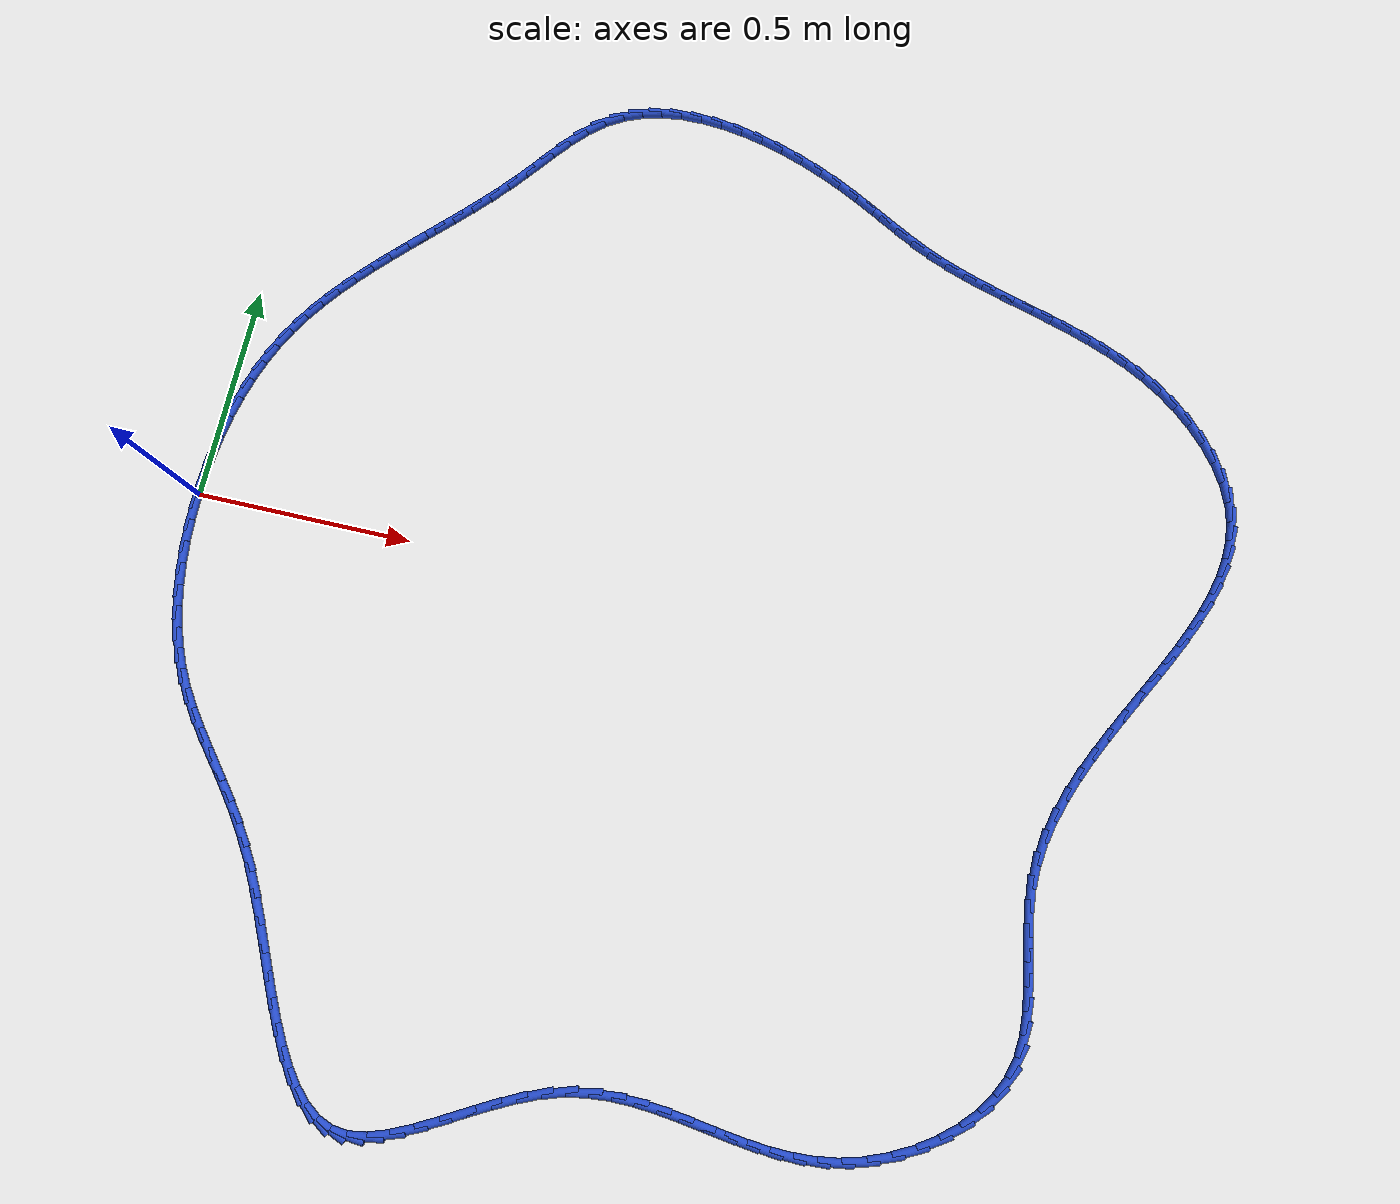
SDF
<sdf version="1.6">
 <world name="default">
  <light name="sun" type="directional">
   <pose>0 0 10 0 -0 0</pose>
   <diffuse>0.8 0.8 0.8 1</diffuse>
   <specular>0.2 0.2 0.2 1</specular>
   <attenuation>
    <range>1000</range>
    <constant>0.9</constant>
    <linear>0.01</linear>
    <quadratic>0.001</quadratic>
   </attenuation>
   <direction>-0.5 0.1 -0.9</direction>
  </light>
  <model name="ground_plane">
   <static>1</static>
   <link name="link">
    <collision name="collision">
     <geometry><plane><normal>0 0 1</normal><size>100 100</size></plane></geometry>
     <surface><friction><ode><mu>100</mu><mu2>50</mu2></ode></friction></surface>
    </collision>
    <visual name="visual">
     <cast_shadows>0</cast_shadows>
     <geometry><plane><normal>0 0 1</normal><size>100 100</size></plane></geometry>
     <material>
      <script><uri>file://media/materials/scripts/gazebo.material</uri><name>Gazebo/WhiteGlow</name></script>
     </material>
    </visual>
   </link>
  </model>
  <gravity>0 0 -9.8</gravity>
  <magnetic_field>6e-06 2.3e-05 -4.2e-05</magnetic_field>
  <atmosphere type="adiabatic"/>
  <physics name="default_physics" default="0" type="ode">
   <max_step_size>0.001</max_step_size>
   <real_time_factor>1</real_time_factor>
   <real_time_update_rate>1000</real_time_update_rate>
  </physics>
  <scene><ambient>0.4 0.4 0.4 1</ambient><background>0.7 0.7 0.7 1</background><shadows>1</shadows></scene>
  <spherical_coordinates>
   <surface_model>EARTH_WGS84</surface_model>
   <latitude_deg>0</latitude_deg>
   <longitude_deg>0</longitude_deg>
   <elevation>0</elevation>
   <heading_deg>0</heading_deg>
  </spherical_coordinates>
  <model name="line">
   <link name="link_0">
    <pose>-3.8163916471489756e-17 -6.938893903907228e-17 0.01 0 1.57 1.5462756870200094</pose>
    <collision name="collision">
     <geometry><cylinder><radius>0.01</radius><length>0.08</length></cylinder></geometry>
    </collision>
    <visual name="visual">
     <material>
      <script><name>Gazebo/Blue</name><uri>file://media/materials/scripts/gazebo.material</uri></script>
     </material>
     <geometry><cylinder><radius>0.01</radius><length>0.08</length></cylinder></geometry>
    </visual>
   </link>
   <link name="link_1">
    <pose>0.0012672009260338462 0.05166859243172 0.01 0 1.57 1.502393266471117</pose>
    <collision name="collision">
     <geometry><cylinder><radius>0.01</radius><length>0.08</length></cylinder></geometry>
    </collision>
    <visual name="visual">
     <material>
      <script><name>Gazebo/Blue</name><uri>file://media/materials/scripts/gazebo.material</uri></script>
     </material>
     <geometry><cylinder><radius>0.01</radius><length>0.08</length></cylinder></geometry>
    </visual>
   </link>
   <link name="link_2">
    <pose>0.004782046874387346 0.10297276300416074 0.01 0 1.57 1.4556271245263754</pose>
    <collision name="collision">
     <geometry><cylinder><radius>0.01</radius><length>0.08</length></cylinder></geometry>
    </collision>
    <visual name="visual">
     <material>
      <script><name>Gazebo/Blue</name><uri>file://media/materials/scripts/gazebo.material</uri></script>
     </material>
     <geometry><cylinder><radius>0.01</radius><length>0.08</length></cylinder></geometry>
    </visual>
   </link>
   <link name="link_3">
    <pose>0.010650732320014854 0.15370433924145888 0.01 0 1.57 1.4055778288071707</pose>
    <collision name="collision">
     <geometry><cylinder><radius>0.01</radius><length>0.08</length></cylinder></geometry>
    </collision>
    <visual name="visual">
     <material>
      <script><name>Gazebo/Blue</name><uri>file://media/materials/scripts/gazebo.material</uri></script>
     </material>
     <geometry><cylinder><radius>0.01</radius><length>0.08</length></cylinder></geometry>
    </visual>
   </link>
   <link name="link_4">
    <pose>0.018979451737870794 0.2036551486677512 0.01 0 1.57 1.3518445580672431</pose>
    <collision name="collision">
     <geometry><cylinder><radius>0.01</radius><length>0.08</length></cylinder></geometry>
    </collision>
    <visual name="visual">
     <material>
      <script><name>Gazebo/Blue</name><uri>file://media/materials/scripts/gazebo.material</uri></script>
     </material>
     <geometry><cylinder><radius>0.01</radius><length>0.08</length></cylinder></geometry>
    </visual>
   </link>
   <link name="link_5">
    <pose>0.029874399602909555 0.2526170188071743 0.01 0 1.57 1.2940400681866113</pose>
    <collision name="collision">
     <geometry><cylinder><radius>0.01</radius><length>0.08</length></cylinder></geometry>
    </collision>
    <visual name="visual">
     <material>
      <script><name>Gazebo/Blue</name><uri>file://media/materials/scripts/gazebo.material</uri></script>
     </material>
     <geometry><cylinder><radius>0.01</radius><length>0.08</length></cylinder></geometry>
    </visual>
   </link>
   <link name="link_6">
    <pose>0.04344177039008556 0.3003817771838649 0.01 0 1.57 1.2318140821504533</pose>
    <collision name="collision">
     <geometry><cylinder><radius>0.01</radius><length>0.08</length></cylinder></geometry>
    </collision>
    <visual name="visual">
     <material>
      <script><name>Gazebo/Blue</name><uri>file://media/materials/scripts/gazebo.material</uri></script>
     </material>
     <geometry><cylinder><radius>0.01</radius><length>0.08</length></cylinder></geometry>
    </visual>
   </link>
   <link name="link_7">
    <pose>0.0597877585743532 0.34674125132195976 0.01 0 1.57 1.1648866564142413</pose>
    <collision name="collision">
     <geometry><cylinder><radius>0.01</radius><length>0.08</length></cylinder></geometry>
    </collision>
    <visual name="visual">
     <material>
      <script><name>Gazebo/Blue</name><uri>file://media/materials/scripts/gazebo.material</uri></script>
     </material>
     <geometry><cylinder><radius>0.01</radius><length>0.08</length></cylinder></geometry>
    </visual>
   </link>
   <link name="link_8">
    <pose>0.07901855863066692 0.3914872687455957 0.01 0 1.57 1.0936525798579175</pose>
    <collision name="collision">
     <geometry><cylinder><radius>0.01</radius><length>0.08</length></cylinder></geometry>
    </collision>
    <visual name="visual">
     <material>
      <script><name>Gazebo/Blue</name><uri>file://media/materials/scripts/gazebo.material</uri></script>
     </material>
     <geometry><cylinder><radius>0.01</radius><length>0.08</length></cylinder></geometry>
    </visual>
   </link>
   <link name="link_9">
    <pose>0.1012205721681377 0.4344323795262763 0.01 0 1.57 1.025270810023189</pose>
    <collision name="collision">
     <geometry><cylinder><radius>0.01</radius><length>0.08</length></cylinder></geometry>
    </collision>
    <visual name="visual">
     <material>
      <script><name>Gazebo/Blue</name><uri>file://media/materials/scripts/gazebo.material</uri></script>
     </material>
     <geometry><cylinder><radius>0.01</radius><length>0.08</length></cylinder></geometry>
    </visual>
   </link>
   <link name="link_10">
    <pose>0.12623544718034968 0.4756453835596192 0.01 0 1.57 0.9651843494109622</pose>
    <collision name="collision">
     <geometry><cylinder><radius>0.01</radius><length>0.08</length></cylinder></geometry>
    </collision>
    <visual name="visual">
     <material>
      <script><name>Gazebo/Blue</name><uri>file://media/materials/scripts/gazebo.material</uri></script>
     </material>
     <geometry><cylinder><radius>0.01</radius><length>0.08</length></cylinder></geometry>
    </visual>
   </link>
   <link name="link_11">
    <pose>0.15373967337440875 0.5153679966010128 0.01 0 1.57 0.9139728003465949</pose>
    <collision name="collision">
     <geometry><cylinder><radius>0.01</radius><length>0.08</length></cylinder></geometry>
    </collision>
    <visual name="visual">
     <material>
      <script><name>Gazebo/Blue</name><uri>file://media/materials/scripts/gazebo.material</uri></script>
     </material>
     <geometry><cylinder><radius>0.01</radius><length>0.08</length></cylinder></geometry>
    </visual>
   </link>
   <link name="link_12">
    <pose>0.1834066428311617 0.5538451775292715 0.01 0 1.57 0.8717819418755589</pose>
    <collision name="collision">
     <geometry><cylinder><radius>0.01</radius><length>0.08</length></cylinder></geometry>
    </collision>
    <visual name="visual">
     <material>
      <script><name>Gazebo/Blue</name><uri>file://media/materials/scripts/gazebo.material</uri></script>
     </material>
     <geometry><cylinder><radius>0.01</radius><length>0.08</length></cylinder></geometry>
    </visual>
   </link>
   <link name="link_13">
    <pose>0.21490974763145532 0.5913218852232094 0.01 0 1.57 0.8385297779313536</pose>
    <collision name="collision">
     <geometry><cylinder><radius>0.01</radius><length>0.08</length></cylinder></geometry>
    </collision>
    <visual name="visual">
     <material>
      <script><name>Gazebo/Blue</name><uri>file://media/materials/scripts/gazebo.material</uri></script>
     </material>
     <geometry><cylinder><radius>0.01</radius><length>0.08</length></cylinder></geometry>
    </visual>
   </link>
   <link name="link_14">
    <pose>0.2479223798561363 0.6280430785616407 0.01 0 1.57 0.8140112184688358</pose>
    <collision name="collision">
     <geometry><cylinder><radius>0.01</radius><length>0.08</length></cylinder></geometry>
    </collision>
    <visual name="visual">
     <material>
      <script><name>Gazebo/Blue</name><uri>file://media/materials/scripts/gazebo.material</uri></script>
     </material>
     <geometry><cylinder><radius>0.01</radius><length>0.08</length></cylinder></geometry>
    </visual>
   </link>
   <link name="link_15">
    <pose>0.2821179315860514 0.6642537164233795 0.01 0 1.57 0.7979780193318727</pose>
    <collision name="collision">
     <geometry><cylinder><radius>0.01</radius><length>0.08</length></cylinder></geometry>
    </collision>
    <visual name="visual">
     <material>
      <script><name>Gazebo/Blue</name><uri>file://media/materials/scripts/gazebo.material</uri></script>
     </material>
     <geometry><cylinder><radius>0.01</radius><length>0.08</length></cylinder></geometry>
    </visual>
   </link>
   <link name="link_16">
    <pose>0.3171697949020476 0.7001987576872405 0.01 0 1.57 0.7901926432486641</pose>
    <collision name="collision">
     <geometry><cylinder><radius>0.01</radius><length>0.08</length></cylinder></geometry>
    </collision>
    <visual name="visual">
     <material>
      <script><name>Gazebo/Blue</name><uri>file://media/materials/scripts/gazebo.material</uri></script>
     </material>
     <geometry><cylinder><radius>0.01</radius><length>0.08</length></cylinder></geometry>
    </visual>
   </link>
   <link name="link_17">
    <pose>0.3527513618849715 0.7361231612320375 0.01 0 1.57 0.7904592188882107</pose>
    <collision name="collision">
     <geometry><cylinder><radius>0.01</radius><length>0.08</length></cylinder></geometry>
    </collision>
    <visual name="visual">
     <material>
      <script><name>Gazebo/Blue</name><uri>file://media/materials/scripts/gazebo.material</uri></script>
     </material>
     <geometry><cylinder><radius>0.01</radius><length>0.08</length></cylinder></geometry>
    </visual>
   </link>
   <link name="link_18">
    <pose>0.38853602461566983 0.7722718859365848 0.01 0 1.57 0.798635704545894</pose>
    <collision name="collision">
     <geometry><cylinder><radius>0.01</radius><length>0.08</length></cylinder></geometry>
    </collision>
    <visual name="visual">
     <material>
      <script><name>Gazebo/Blue</name><uri>file://media/materials/scripts/gazebo.material</uri></script>
     </material>
     <geometry><cylinder><radius>0.01</radius><length>0.08</length></cylinder></geometry>
    </visual>
   </link>
   <link name="link_19">
    <pose>0.42419717517498967 0.8088898906796973 0.01 0 1.57 0.8146304936156704</pose>
    <collision name="collision">
     <geometry><cylinder><radius>0.01</radius><length>0.08</length></cylinder></geometry>
    </collision>
    <visual name="visual">
     <material>
      <script><name>Gazebo/Blue</name><uri>file://media/materials/scripts/gazebo.material</uri></script>
     </material>
     <geometry><cylinder><radius>0.01</radius><length>0.08</length></cylinder></geometry>
    </visual>
   </link>
   <link name="link_20">
    <pose>0.45940820564377716 0.8462221343401879 0.01 0 1.57 0.838385294227599</pose>
    <collision name="collision">
     <geometry><cylinder><radius>0.01</radius><length>0.08</length></cylinder></geometry>
    </collision>
    <visual name="visual">
     <material>
      <script><name>Gazebo/Blue</name><uri>file://media/materials/scripts/gazebo.material</uri></script>
     </material>
     <geometry><cylinder><radius>0.01</radius><length>0.08</length></cylinder></geometry>
    </visual>
   </link>
   <link name="link_21">
    <pose>0.49384250810287994 0.8845135757968723 0.01 0 1.57 0.8698449691581831</pose>
    <collision name="collision">
     <geometry><cylinder><radius>0.01</radius><length>0.08</length></cylinder></geometry>
    </collision>
    <visual name="visual">
     <material>
      <script><name>Gazebo/Blue</name><uri>file://media/materials/scripts/gazebo.material</uri></script>
     </material>
     <geometry><cylinder><radius>0.01</radius><length>0.08</length></cylinder></geometry>
    </visual>
   </link>
   <link name="link_22">
    <pose>0.5271734746331441 0.9240091739285636 0.01 0 1.57 0.9033022148555317</pose>
    <collision name="collision">
     <geometry><cylinder><radius>0.01</radius><length>0.08</length></cylinder></geometry>
    </collision>
    <visual name="visual">
     <material>
      <script><name>Gazebo/Blue</name><uri>file://media/materials/scripts/gazebo.material</uri></script>
     </material>
     <geometry><cylinder><radius>0.01</radius><length>0.08</length></cylinder></geometry>
    </visual>
   </link>
   <link name="link_23">
    <pose>0.5592529554302327 0.9647096972328136 0.01 0 1.57 0.9096914081871098</pose>
    <collision name="collision">
     <geometry><cylinder><radius>0.01</radius><length>0.08</length></cylinder></geometry>
    </collision>
    <visual name="visual">
     <material>
      <script><name>Gazebo/Blue</name><uri>file://media/materials/scripts/gazebo.material</uri></script>
     </material>
     <geometry><cylinder><radius>0.01</radius><length>0.08</length></cylinder></geometry>
    </visual>
   </link>
   <link name="link_24">
    <pose>0.5908619017973593 1.0053445931808394 0.01 0 1.57 0.8788644872899266</pose>
    <collision name="collision">
     <geometry><cylinder><radius>0.01</radius><length>0.08</length></cylinder></geometry>
    </collision>
    <visual name="visual">
     <material>
      <script><name>Gazebo/Blue</name><uri>file://media/materials/scripts/gazebo.material</uri></script>
     </material>
     <geometry><cylinder><radius>0.01</radius><length>0.08</length></cylinder></geometry>
    </visual>
   </link>
   <link name="link_25">
    <pose>0.6230826649361982 1.0442308933882185 0.01 0 1.57 0.8075862672323947</pose>
    <collision name="collision">
     <geometry><cylinder><radius>0.01</radius><length>0.08</length></cylinder></geometry>
    </collision>
    <visual name="visual">
     <material>
      <script><name>Gazebo/Blue</name><uri>file://media/materials/scripts/gazebo.material</uri></script>
     </material>
     <geometry><cylinder><radius>0.01</radius><length>0.08</length></cylinder></geometry>
    </visual>
   </link>
   <link name="link_26">
    <pose>0.6569977532224126 1.0796854144039498 0.01 0 1.57 0.6909134692510166</pose>
    <collision name="collision">
     <geometry><cylinder><radius>0.01</radius><length>0.08</length></cylinder></geometry>
    </collision>
    <visual name="visual">
     <material>
      <script><name>Gazebo/Blue</name><uri>file://media/materials/scripts/gazebo.material</uri></script>
     </material>
     <geometry><cylinder><radius>0.01</radius><length>0.08</length></cylinder></geometry>
    </visual>
   </link>
   <link name="link_27">
    <pose>0.6936896750316655 1.110024972777031 0.01 0 1.57 0.5324112724979416</pose>
    <collision name="collision">
     <geometry><cylinder><radius>0.01</radius><length>0.08</length></cylinder></geometry>
    </collision>
    <visual name="visual">
     <material>
      <script><name>Gazebo/Blue</name><uri>file://media/materials/scripts/gazebo.material</uri></script>
     </material>
     <geometry><cylinder><radius>0.01</radius><length>0.08</length></cylinder></geometry>
    </visual>
   </link>
   <link name="link_28">
    <pose>0.7340582442324246 1.1338085456849667 0.01 0 1.57 0.37359606067586054</pose>
    <collision name="collision">
     <geometry><cylinder><radius>0.01</radius><length>0.08</length></cylinder></geometry>
    </collision>
    <visual name="visual">
     <material>
      <script><name>Gazebo/Blue</name><uri>file://media/materials/scripts/gazebo.material</uri></script>
     </material>
     <geometry><cylinder><radius>0.01</radius><length>0.08</length></cylinder></geometry>
    </visual>
   </link>
   <link name="link_29">
    <pose>0.7779365170944367 1.1510090920091336 0.01 0 1.57 0.2327538355196856</pose>
    <collision name="collision">
     <geometry><cylinder><radius>0.01</radius><length>0.08</length></cylinder></geometry>
    </collision>
    <visual name="visual">
     <material>
      <script><name>Gazebo/Blue</name><uri>file://media/materials/scripts/gazebo.material</uri></script>
     </material>
     <geometry><cylinder><radius>0.01</radius><length>0.08</length></cylinder></geometry>
    </visual>
   </link>
   <link name="link_30">
    <pose>0.8247714683637739 1.1621113197024202 0.01 0 1.57 0.11102685341370921</pose>
    <collision name="collision">
     <geometry><cylinder><radius>0.01</radius><length>0.08</length></cylinder></geometry>
    </collision>
    <visual name="visual">
     <material>
      <script><name>Gazebo/Blue</name><uri>file://media/materials/scripts/gazebo.material</uri></script>
     </material>
     <geometry><cylinder><radius>0.01</radius><length>0.08</length></cylinder></geometry>
    </visual>
   </link>
   <link name="link_31">
    <pose>0.8740095406577862 1.1676006420515974 0.01 0 1.57 0.007082422885703143</pose>
    <collision name="collision">
     <geometry><cylinder><radius>0.01</radius><length>0.08</length></cylinder></geometry>
    </collision>
    <visual name="visual">
     <material>
      <script><name>Gazebo/Blue</name><uri>file://media/materials/scripts/gazebo.material</uri></script>
     </material>
     <geometry><cylinder><radius>0.01</radius><length>0.08</length></cylinder></geometry>
    </visual>
   </link>
   <link name="link_32">
    <pose>0.9250971765938225 1.167962472343436 0.01 0 1.57 -0.08152851986114676</pose>
    <collision name="collision">
     <geometry><cylinder><radius>0.01</radius><length>0.08</length></cylinder></geometry>
    </collision>
    <visual name="visual">
     <material>
      <script><name>Gazebo/Blue</name><uri>file://media/materials/scripts/gazebo.material</uri></script>
     </material>
     <geometry><cylinder><radius>0.01</radius><length>0.08</length></cylinder></geometry>
    </visual>
   </link>
   <link name="link_33">
    <pose>0.9774808187892332 1.1636822238647089 0.01 0 1.57 -0.15749400615234294</pose>
    <collision name="collision">
     <geometry><cylinder><radius>0.01</radius><length>0.08</length></cylinder></geometry>
    </collision>
    <visual name="visual">
     <material>
      <script><name>Gazebo/Blue</name><uri>file://media/materials/scripts/gazebo.material</uri></script>
     </material>
     <geometry><cylinder><radius>0.01</radius><length>0.08</length></cylinder></geometry>
    </visual>
   </link>
   <link name="link_34">
    <pose>1.0306069098613677 1.1552453099021864 0.01 0 1.57 -0.22331830199385183</pose>
    <collision name="collision">
     <geometry><cylinder><radius>0.01</radius><length>0.08</length></cylinder></geometry>
    </collision>
    <visual name="visual">
     <material>
      <script><name>Gazebo/Blue</name><uri>file://media/materials/scripts/gazebo.material</uri></script>
     </material>
     <geometry><cylinder><radius>0.01</radius><length>0.08</length></cylinder></geometry>
    </visual>
   </link>
   <link name="link_35">
    <pose>1.0839218924275749 1.1431371437426399 0.01 0 1.57 -0.2811842125609918</pose>
    <collision name="collision">
     <geometry><cylinder><radius>0.01</radius><length>0.08</length></cylinder></geometry>
    </collision>
    <visual name="visual">
     <material>
      <script><name>Gazebo/Blue</name><uri>file://media/materials/scripts/gazebo.material</uri></script>
     </material>
     <geometry><cylinder><radius>0.01</radius><length>0.08</length></cylinder></geometry>
    </visual>
   </link>
   <link name="link_36">
    <pose>1.1368722091052053 1.127843138672841 0.01 0 1.57 -0.33295802760124027</pose>
    <collision name="collision">
     <geometry><cylinder><radius>0.01</radius><length>0.08</length></cylinder></geometry>
    </collision>
    <visual name="visual">
     <material>
      <script><name>Gazebo/Blue</name><uri>file://media/materials/scripts/gazebo.material</uri></script>
     </material>
     <geometry><cylinder><radius>0.01</radius><length>0.08</length></cylinder></geometry>
    </visual>
   </link>
   <link name="link_37">
    <pose>1.1889043025116077 1.1098487079795605 0.01 0 1.57 -0.38025601819773913</pose>
    <collision name="collision">
     <geometry><cylinder><radius>0.01</radius><length>0.08</length></cylinder></geometry>
    </collision>
    <visual name="visual">
     <material>
      <script><name>Gazebo/Blue</name><uri>file://media/materials/scripts/gazebo.material</uri></script>
     </material>
     <geometry><cylinder><radius>0.01</radius><length>0.08</length></cylinder></geometry>
    </visual>
   </link>
   <link name="link_38">
    <pose>1.2394646152641324 1.08963926494957 0.01 0 1.57 -0.4245283396938669</pose>
    <collision name="collision">
     <geometry><cylinder><radius>0.01</radius><length>0.08</length></cylinder></geometry>
    </collision>
    <visual name="visual">
     <material>
      <script><name>Gazebo/Blue</name><uri>file://media/materials/scripts/gazebo.material</uri></script>
     </material>
     <geometry><cylinder><radius>0.01</radius><length>0.08</length></cylinder></geometry>
    </visual>
   </link>
   <link name="link_39">
    <pose>1.288000413019827 1.0677003562073164 0.01 0 1.57 -0.46350981282754633</pose>
    <collision name="collision">
     <geometry><cylinder><radius>0.01</radius><length>0.08</length></cylinder></geometry>
    </collision>
    <visual name="visual">
     <material>
      <script><name>Gazebo/Blue</name><uri>file://media/materials/scripts/gazebo.material</uri></script>
     </material>
     <geometry><cylinder><radius>0.01</radius><length>0.08</length></cylinder></geometry>
    </visual>
   </link>
   <link name="link_40">
    <pose>1.334278481395089 1.044569292646485 0.01 0 1.57 -0.4877704352281412</pose>
    <collision name="collision">
     <geometry><cylinder><radius>0.01</radius><length>0.08</length></cylinder></geometry>
    </collision>
    <visual name="visual">
     <material>
      <script><name>Gazebo/Blue</name><uri>file://media/materials/scripts/gazebo.material</uri></script>
     </material>
     <geometry><cylinder><radius>0.01</radius><length>0.08</length></cylinder></geometry>
    </visual>
   </link>
   <link name="link_41">
    <pose>1.378867915565967 1.0209133644213495 0.01 0 1.57 -0.49429398240632344</pose>
    <collision name="collision">
     <geometry><cylinder><radius>0.01</radius><length>0.08</length></cylinder></geometry>
    </collision>
    <visual name="visual">
     <material>
      <script><name>Gazebo/Blue</name><uri>file://media/materials/scripts/gazebo.material</uri></script>
     </material>
     <geometry><cylinder><radius>0.01</radius><length>0.08</length></cylinder></geometry>
    </visual>
   </link>
   <link name="link_42">
    <pose>1.4224617331340297 0.997419937908691 0.01 0 1.57 -0.4819186823524124</pose>
    <collision name="collision">
     <geometry><cylinder><radius>0.01</radius><length>0.08</length></cylinder></geometry>
    </collision>
    <visual name="visual">
     <material>
      <script><name>Gazebo/Blue</name><uri>file://media/materials/scripts/gazebo.material</uri></script>
     </material>
     <geometry><cylinder><radius>0.01</radius><length>0.08</length></cylinder></geometry>
    </visual>
   </link>
   <link name="link_43">
    <pose>1.4657529517008454 0.9747763794852897 0.01 0 1.57 -0.45010557070894686</pose>
    <collision name="collision">
     <geometry><cylinder><radius>0.01</radius><length>0.08</length></cylinder></geometry>
    </collision>
    <visual name="visual">
     <material>
      <script><name>Gazebo/Blue</name><uri>file://media/materials/scripts/gazebo.material</uri></script>
     </material>
     <geometry><cylinder><radius>0.01</radius><length>0.08</length></cylinder></geometry>
    </visual>
   </link>
   <link name="link_44">
    <pose>1.5094345888679837 0.9536700555279268 0.01 0 1.57 -0.40035812389498227</pose>
    <collision name="collision">
     <geometry><cylinder><radius>0.01</radius><length>0.08</length></cylinder></geometry>
    </collision>
    <visual name="visual">
     <material>
      <script><name>Gazebo/Blue</name><uri>file://media/materials/scripts/gazebo.material</uri></script>
     </material>
     <geometry><cylinder><radius>0.01</radius><length>0.08</length></cylinder></geometry>
    </visual>
   </link>
   <link name="link_45">
    <pose>1.5541625938978998 0.9347404739728999 0.01 0 1.57 -0.35026342725918364</pose>
    <collision name="collision">
     <geometry><cylinder><radius>0.01</radius><length>0.08</length></cylinder></geometry>
    </collision>
    <visual name="visual">
     <material>
      <script><name>Gazebo/Blue</name><uri>file://media/materials/scripts/gazebo.material</uri></script>
     </material>
     <geometry><cylinder><radius>0.01</radius><length>0.08</length></cylinder></geometry>
    </visual>
   </link>
   <link name="link_46">
    <pose>1.6000804103710453 0.9179654534748806 0.01 0 1.57 -0.3121177123310492</pose>
    <collision name="collision">
     <geometry><cylinder><radius>0.01</radius><length>0.08</length></cylinder></geometry>
    </collision>
    <visual name="visual">
     <material>
      <script><name>Gazebo/Blue</name><uri>file://media/materials/scripts/gazebo.material</uri></script>
     </material>
     <geometry><cylinder><radius>0.01</radius><length>0.08</length></cylinder></geometry>
    </visual>
   </link>
   <link name="link_47">
    <pose>1.6469574564346314 0.9028399134175215 0.01 0 1.57 -0.2859151595598011</pose>
    <collision name="collision">
     <geometry><cylinder><radius>0.01</radius><length>0.08</length></cylinder></geometry>
    </collision>
    <visual name="visual">
     <material>
      <script><name>Gazebo/Blue</name><uri>file://media/materials/scripts/gazebo.material</uri></script>
     </material>
     <geometry><cylinder><radius>0.01</radius><length>0.08</length></cylinder></geometry>
    </visual>
   </link>
   <link name="link_48">
    <pose>1.694554642234472 0.8888477886168304 0.01 0 1.57 -0.27132738609206714</pose>
    <collision name="collision">
     <geometry><cylinder><radius>0.01</radius><length>0.08</length></cylinder></geometry>
    </collision>
    <visual name="visual">
     <material>
      <script><name>Gazebo/Blue</name><uri>file://media/materials/scripts/gazebo.material</uri></script>
     </material>
     <geometry><cylinder><radius>0.01</radius><length>0.08</length></cylinder></geometry>
    </visual>
   </link>
   <link name="link_49">
    <pose>1.74263287791638 0.8754730138888163 0.01 0 1.57 -0.26808597486838165</pose>
    <collision name="collision">
     <geometry><cylinder><radius>0.01</radius><length>0.08</length></cylinder></geometry>
    </collision>
    <visual name="visual">
     <material>
      <script><name>Gazebo/Blue</name><uri>file://media/materials/scripts/gazebo.material</uri></script>
     </material>
     <geometry><cylinder><radius>0.01</radius><length>0.08</length></cylinder></geometry>
    </visual>
   </link>
   <link name="link_50">
    <pose>1.7909530736261712 0.8621995240494872 0.01 0 1.57 -0.27603446937864645</pose>
    <collision name="collision">
     <geometry><cylinder><radius>0.01</radius><length>0.08</length></cylinder></geometry>
    </collision>
    <visual name="visual">
     <material>
      <script><name>Gazebo/Blue</name><uri>file://media/materials/scripts/gazebo.material</uri></script>
     </material>
     <geometry><cylinder><radius>0.01</radius><length>0.08</length></cylinder></geometry>
    </visual>
   </link>
   <link name="link_51">
    <pose>1.8392761395096586 0.8485112539148516 0.01 0 1.57 -0.2951360661776336</pose>
    <collision name="collision">
     <geometry><cylinder><radius>0.01</radius><length>0.08</length></cylinder></geometry>
    </collision>
    <visual name="visual">
     <material>
      <script><name>Gazebo/Blue</name><uri>file://media/materials/scripts/gazebo.material</uri></script>
     </material>
     <geometry><cylinder><radius>0.01</radius><length>0.08</length></cylinder></geometry>
    </visual>
   </link>
   <link name="link_52">
    <pose>1.8873629857126564 0.833892138300918 0.01 0 1.57 -0.3254417888255941</pose>
    <collision name="collision">
     <geometry><cylinder><radius>0.01</radius><length>0.08</length></cylinder></geometry>
    </collision>
    <visual name="visual">
     <material>
      <script><name>Gazebo/Blue</name><uri>file://media/materials/scripts/gazebo.material</uri></script>
     </material>
     <geometry><cylinder><radius>0.01</radius><length>0.08</length></cylinder></geometry>
    </visual>
   </link>
   <link name="link_53">
    <pose>1.934974522380978 0.8178261120236942 0.01 0 1.57 -0.3670185643590996</pose>
    <collision name="collision">
     <geometry><cylinder><radius>0.01</radius><length>0.08</length></cylinder></geometry>
    </collision>
    <visual name="visual">
     <material>
      <script><name>Gazebo/Blue</name><uri>file://media/materials/scripts/gazebo.material</uri></script>
     </material>
     <geometry><cylinder><radius>0.01</radius><length>0.08</length></cylinder></geometry>
    </visual>
   </link>
   <link name="link_54">
    <pose>1.9818716596604384 0.7997971098991886 0.01 0 1.57 -0.4198343302029406</pose>
    <collision name="collision">
     <geometry><cylinder><radius>0.01</radius><length>0.08</length></cylinder></geometry>
    </collision>
    <visual name="visual">
     <material>
      <script><name>Gazebo/Blue</name><uri>file://media/materials/scripts/gazebo.material</uri></script>
     </material>
     <geometry><cylinder><radius>0.01</radius><length>0.08</length></cylinder></geometry>
    </visual>
   </link>
   <link name="link_55">
    <pose>2.0278153076968506 0.77928906674341 0.01 0 1.57 -0.48360181227801835</pose>
    <collision name="collision">
     <geometry><cylinder><radius>0.01</radius><length>0.08</length></cylinder></geometry>
    </collision>
    <visual name="visual">
     <material>
      <script><name>Gazebo/Blue</name><uri>file://media/materials/scripts/gazebo.material</uri></script>
     </material>
     <geometry><cylinder><radius>0.01</radius><length>0.08</length></cylinder></geometry>
    </visual>
   </link>
   <link name="link_56">
    <pose>2.072566376636029 0.7557859173723664 0.01 0 1.57 -0.557597640164174</pose>
    <collision name="collision">
     <geometry><cylinder><radius>0.01</radius><length>0.08</length></cylinder></geometry>
    </collision>
    <visual name="visual">
     <material>
      <script><name>Gazebo/Blue</name><uri>file://media/materials/scripts/gazebo.material</uri></script>
     </material>
     <geometry><cylinder><radius>0.01</radius><length>0.08</length></cylinder></geometry>
    </visual>
   </link>
   <link name="link_57">
    <pose>2.115885776623789 0.7287715966020665 0.01 0 1.57 -0.639975336477577</pose>
    <collision name="collision">
     <geometry><cylinder><radius>0.01</radius><length>0.08</length></cylinder></geometry>
    </collision>
    <visual name="visual">
     <material>
      <script><name>Gazebo/Blue</name><uri>file://media/materials/scripts/gazebo.material</uri></script>
     </material>
     <geometry><cylinder><radius>0.01</radius><length>0.08</length></cylinder></geometry>
    </visual>
   </link>
   <link name="link_58">
    <pose>2.1574827591603647 0.6978024148488906 0.01 0 1.57 -0.7255757063611656</pose>
    <collision name="collision">
     <geometry><cylinder><radius>0.01</radius><length>0.08</length></cylinder></geometry>
    </collision>
    <visual name="visual">
     <material>
      <script><name>Gazebo/Blue</name><uri>file://media/materials/scripts/gazebo.material</uri></script>
     </material>
     <geometry><cylinder><radius>0.01</radius><length>0.08</length></cylinder></geometry>
    </visual>
   </link>
   <link name="link_59">
    <pose>2.196565407601197 0.6631368369307228 0.01 0 1.57 -0.8156354795578555</pose>
    <collision name="collision">
     <geometry><cylinder><radius>0.01</radius><length>0.08</length></cylinder></geometry>
    </collision>
    <visual name="visual">
     <material>
      <script><name>Gazebo/Blue</name><uri>file://media/materials/scripts/gazebo.material</uri></script>
     </material>
     <geometry><cylinder><radius>0.01</radius><length>0.08</length></cylinder></geometry>
    </visual>
   </link>
   <link name="link_60">
    <pose>2.232060146209422 0.6254279420746713 0.01 0 1.57 -0.9152886023386736</pose>
    <collision name="collision">
     <geometry><cylinder><radius>0.01</radius><length>0.08</length></cylinder></geometry>
    </collision>
    <visual name="visual">
     <material>
      <script><name>Gazebo/Blue</name><uri>file://media/materials/scripts/gazebo.material</uri></script>
     </material>
     <geometry><cylinder><radius>0.01</radius><length>0.08</length></cylinder></geometry>
    </visual>
   </link>
   <link name="link_61">
    <pose>2.262890266235847 0.5853331989695864 0.01 0 1.57 -1.0304661588988793</pose>
    <collision name="collision">
     <geometry><cylinder><radius>0.01</radius><length>0.08</length></cylinder></geometry>
    </collision>
    <visual name="visual">
     <material>
      <script><name>Gazebo/Blue</name><uri>file://media/materials/scripts/gazebo.material</uri></script>
     </material>
     <geometry><cylinder><radius>0.01</radius><length>0.08</length></cylinder></geometry>
    </visual>
   </link>
   <link name="link_62">
    <pose>2.28797905893128 0.5435100763043171 0.01 0 1.57 -1.168051368587633</pose>
    <collision name="collision">
     <geometry><cylinder><radius>0.01</radius><length>0.08</length></cylinder></geometry>
    </collision>
    <visual name="visual">
     <material>
      <script><name>Gazebo/Blue</name><uri>file://media/materials/scripts/gazebo.material</uri></script>
     </material>
     <geometry><cylinder><radius>0.01</radius><length>0.08</length></cylinder></geometry>
    </visual>
   </link>
   <link name="link_63">
    <pose>2.306253957776105 0.5006145370645906 0.01 0 1.57 -1.3245790183814914</pose>
    <collision name="collision">
     <geometry><cylinder><radius>0.01</radius><length>0.08</length></cylinder></geometry>
    </collision>
    <visual name="visual">
     <material>
      <script><name>Gazebo/Blue</name><uri>file://media/materials/scripts/gazebo.material</uri></script>
     </material>
     <geometry><cylinder><radius>0.01</radius><length>0.08</length></cylinder></geometry>
    </visual>
   </link>
   <link name="link_64">
    <pose>2.3171889000173245 0.45710388976432564 0.01 0 1.57 -1.4767651632227605</pose>
    <collision name="collision">
     <geometry><cylinder><radius>0.01</radius><length>0.08</length></cylinder></geometry>
    </collision>
    <visual name="visual">
     <material>
      <script><name>Gazebo/Blue</name><uri>file://media/materials/scripts/gazebo.material</uri></script>
     </material>
     <geometry><cylinder><radius>0.01</radius><length>0.08</length></cylinder></geometry>
    </visual>
   </link>
   <link name="link_65">
    <pose>2.32134449262715 0.41304043777113897 0.01 0 1.57 1.5274452785574018</pose>
    <collision name="collision">
     <geometry><cylinder><radius>0.01</radius><length>0.08</length></cylinder></geometry>
    </collision>
    <visual name="visual">
     <material>
      <script><name>Gazebo/Blue</name><uri>file://media/materials/scripts/gazebo.material</uri></script>
     </material>
     <geometry><cylinder><radius>0.01</radius><length>0.08</length></cylinder></geometry>
    </visual>
   </link>
   <link name="link_66">
    <pose>2.3194097957463073 0.3684397916430053 0.01 0 1.57 1.4096274718913477</pose>
    <collision name="collision">
     <geometry><cylinder><radius>0.01</radius><length>0.08</length></cylinder></geometry>
    </collision>
    <visual name="visual">
     <material>
      <script><name>Gazebo/Blue</name><uri>file://media/materials/scripts/gazebo.material</uri></script>
     </material>
     <geometry><cylinder><radius>0.01</radius><length>0.08</length></cylinder></geometry>
    </visual>
   </link>
   <link name="link_67">
    <pose>2.3120738695155225 0.3233175619378985 0.01 0 1.57 1.3126391138834492</pose>
    <collision name="collision">
     <geometry><cylinder><radius>0.01</radius><length>0.08</length></cylinder></geometry>
    </collision>
    <visual name="visual">
     <material>
      <script><name>Gazebo/Blue</name><uri>file://media/materials/scripts/gazebo.material</uri></script>
     </material>
     <geometry><cylinder><radius>0.01</radius><length>0.08</length></cylinder></geometry>
    </visual>
   </link>
   <link name="link_68">
    <pose>2.3000257740755217 0.27768935921379434 0.01 0 1.57 1.235480002311765</pose>
    <collision name="collision">
     <geometry><cylinder><radius>0.01</radius><length>0.08</length></cylinder></geometry>
    </collision>
    <visual name="visual">
     <material>
      <script><name>Gazebo/Blue</name><uri>file://media/materials/scripts/gazebo.material</uri></script>
     </material>
     <geometry><cylinder><radius>0.01</radius><length>0.08</length></cylinder></geometry>
    </visual>
   </link>
   <link name="link_69">
    <pose>2.2839545695670314 0.23157079402866707 0.01 0 1.57 1.1761630137320203</pose>
    <collision name="collision">
     <geometry><cylinder><radius>0.01</radius><length>0.08</length></cylinder></geometry>
    </collision>
    <visual name="visual">
     <material>
      <script><name>Gazebo/Blue</name><uri>file://media/materials/scripts/gazebo.material</uri></script>
     </material>
     <geometry><cylinder><radius>0.01</radius><length>0.08</length></cylinder></geometry>
    </visual>
   </link>
   <link name="link_70">
    <pose>2.264549316130777 0.18497747694049116 0.01 0 1.57 1.1325573067986086</pose>
    <collision name="collision">
     <geometry><cylinder><radius>0.01</radius><length>0.08</length></cylinder></geometry>
    </collision>
    <visual name="visual">
     <material>
      <script><name>Gazebo/Blue</name><uri>file://media/materials/scripts/gazebo.material</uri></script>
     </material>
     <geometry><cylinder><radius>0.01</radius><length>0.08</length></cylinder></geometry>
    </visual>
   </link>
   <link name="link_71">
    <pose>2.242499073907484 0.13792501850724087 0.01 0 1.57 1.102809580746991</pose>
    <collision name="collision">
     <geometry><cylinder><radius>0.01</radius><length>0.08</length></cylinder></geometry>
    </collision>
    <visual name="visual">
     <material>
      <script><name>Gazebo/Blue</name><uri>file://media/materials/scripts/gazebo.material</uri></script>
     </material>
     <geometry><cylinder><radius>0.01</radius><length>0.08</length></cylinder></geometry>
    </visual>
   </link>
   <link name="link_72">
    <pose>2.2184929030378795 0.09042902928689162 0.01 0 1.57 1.0855029022516212</pose>
    <collision name="collision">
     <geometry><cylinder><radius>0.01</radius><length>0.08</length></cylinder></geometry>
    </collision>
    <visual name="visual">
     <material>
      <script><name>Gazebo/Blue</name><uri>file://media/materials/scripts/gazebo.material</uri></script>
     </material>
     <geometry><cylinder><radius>0.01</radius><length>0.08</length></cylinder></geometry>
    </visual>
   </link>
   <link name="link_73">
    <pose>2.1932198636626903 0.0425051198374178 0.01 0 1.57 1.0796875678186968</pose>
    <collision name="collision">
     <geometry><cylinder><radius>0.01</radius><length>0.08</length></cylinder></geometry>
    </collision>
    <visual name="visual">
     <material>
      <script><name>Gazebo/Blue</name><uri>file://media/materials/scripts/gazebo.material</uri></script>
     </material>
     <geometry><cylinder><radius>0.01</radius><length>0.08</length></cylinder></geometry>
    </visual>
   </link>
   <link name="link_74">
    <pose>2.167369015922641 -0.005831099283206118 0.01 0 1.57 1.084862208632373</pose>
    <collision name="collision">
     <geometry><cylinder><radius>0.01</radius><length>0.08</length></cylinder></geometry>
    </collision>
    <visual name="visual">
     <material>
      <script><name>Gazebo/Blue</name><uri>file://media/materials/scripts/gazebo.material</uri></script>
     </material>
     <geometry><cylinder><radius>0.01</radius><length>0.08</length></cylinder></geometry>
    </visual>
   </link>
   <link name="link_75">
    <pose>2.1416294199584582 -0.05456401751700535 0.01 0 1.57 1.1009412950378603</pose>
    <collision name="collision">
     <geometry><cylinder><radius>0.01</radius><length>0.08</length></cylinder></geometry>
    </collision>
    <visual name="visual">
     <material>
      <script><name>Gazebo/Blue</name><uri>file://media/materials/scripts/gazebo.material</uri></script>
     </material>
     <geometry><cylinder><radius>0.01</radius><length>0.08</length></cylinder></geometry>
    </visual>
   </link>
   <link name="link_76">
    <pose>2.116690135910868 -0.10367802430600577 0.01 0 1.57 1.1282197298183965</pose>
    <collision name="collision">
     <geometry><cylinder><radius>0.01</radius><length>0.08</length></cylinder></geometry>
    </collision>
    <visual name="visual">
     <material>
      <script><name>Gazebo/Blue</name><uri>file://media/materials/scripts/gazebo.material</uri></script>
     </material>
     <geometry><cylinder><radius>0.01</radius><length>0.08</length></cylinder></geometry>
    </visual>
   </link>
   <link name="link_77">
    <pose>2.093240223920596 -0.15315750909223236 0.01 0 1.57 1.1673288482719377</pose>
    <collision name="collision">
     <geometry><cylinder><radius>0.01</radius><length>0.08</length></cylinder></geometry>
    </collision>
    <visual name="visual">
     <material>
      <script><name>Gazebo/Blue</name><uri>file://media/materials/scripts/gazebo.material</uri></script>
     </material>
     <geometry><cylinder><radius>0.01</radius><length>0.08</length></cylinder></geometry>
    </visual>
   </link>
   <link name="link_78">
    <pose>2.0719687441283696 -0.2029868613177095 0.01 0 1.57 1.2191641529187107</pose>
    <collision name="collision">
     <geometry><cylinder><radius>0.01</radius><length>0.08</length></cylinder></geometry>
    </collision>
    <visual name="visual">
     <material>
      <script><name>Gazebo/Blue</name><uri>file://media/materials/scripts/gazebo.material</uri></script>
     </material>
     <geometry><cylinder><radius>0.01</radius><length>0.08</length></cylinder></geometry>
    </visual>
   </link>
   <link name="link_79">
    <pose>2.0535647566749136 -0.25315047042446437 0.01 0 1.57 1.284750121464308</pose>
    <collision name="collision">
     <geometry><cylinder><radius>0.01</radius><length>0.08</length></cylinder></geometry>
    </collision>
    <visual name="visual">
     <material>
      <script><name>Gazebo/Blue</name><uri>file://media/materials/scripts/gazebo.material</uri></script>
     </material>
     <geometry><cylinder><radius>0.01</radius><length>0.08</length></cylinder></geometry>
    </visual>
   </link>
   <link name="link_80">
    <pose>2.038717321700954 -0.3036327258545206 0.01 0 1.57 1.3649942245469102</pose>
    <collision name="collision">
     <geometry><cylinder><radius>0.01</radius><length>0.08</length></cylinder></geometry>
    </collision>
    <visual name="visual">
     <material>
      <script><name>Gazebo/Blue</name><uri>file://media/materials/scripts/gazebo.material</uri></script>
     </material>
     <geometry><cylinder><radius>0.01</radius><length>0.08</length></cylinder></geometry>
    </visual>
   </link>
   <link name="link_81">
    <pose>2.0281154993472175 -0.35441801704990517 0.01 0 1.57 1.4602860364051558</pose>
    <collision name="collision">
     <geometry><cylinder><radius>0.01</radius><length>0.08</length></cylinder></geometry>
    </collision>
    <visual name="visual">
     <material>
      <script><name>Gazebo/Blue</name><uri>file://media/materials/scripts/gazebo.material</uri></script>
     </material>
     <geometry><cylinder><radius>0.01</radius><length>0.08</length></cylinder></geometry>
    </visual>
   </link>
   <link name="link_82">
    <pose>2.0224483497544306 -0.4054907334526427 0.01 0 1.57 1.569283981961905</pose>
    <collision name="collision">
     <geometry><cylinder><radius>0.01</radius><length>0.08</length></cylinder></geometry>
    </collision>
    <visual name="visual">
     <material>
      <script><name>Gazebo/Blue</name><uri>file://media/materials/scripts/gazebo.material</uri></script>
     </material>
     <geometry><cylinder><radius>0.01</radius><length>0.08</length></cylinder></geometry>
    </visual>
   </link>
   <link name="link_83">
    <pose>2.022370703894998 -0.45683206681921423 0.01 0 1.57 -1.4733804726472475</pose>
    <collision name="collision">
     <geometry><cylinder><radius>0.01</radius><length>0.08</length></cylinder></geometry>
    </collision>
    <visual name="visual">
     <material>
      <script><name>Gazebo/Blue</name><uri>file://media/materials/scripts/gazebo.material</uri></script>
     </material>
     <geometry><cylinder><radius>0.01</radius><length>0.08</length></cylinder></geometry>
    </visual>
   </link>
   <link name="link_84">
    <pose>2.02740209296716 -0.5083171493126792 0.01 0 1.57 -1.4108314148797667</pose>
    <collision name="collision">
     <geometry><cylinder><radius>0.01</radius><length>0.08</length></cylinder></geometry>
    </collision>
    <visual name="visual">
     <material>
      <script><name>Gazebo/Blue</name><uri>file://media/materials/scripts/gazebo.material</uri></script>
     </material>
     <geometry><cylinder><radius>0.01</radius><length>0.08</length></cylinder></geometry>
    </visual>
   </link>
   <link name="link_85">
    <pose>2.035691259160511 -0.5596930541215075 0.01 0 1.57 -1.3844981650776136</pose>
    <collision name="collision">
     <geometry><cylinder><radius>0.01</radius><length>0.08</length></cylinder></geometry>
    </collision>
    <visual name="visual">
     <material>
      <script><name>Gazebo/Blue</name><uri>file://media/materials/scripts/gazebo.material</uri></script>
     </material>
     <geometry><cylinder><radius>0.01</radius><length>0.08</length></cylinder></geometry>
    </visual>
   </link>
   <link name="link_86">
    <pose>2.0453050924832916 -0.6106992078114281 0.01 0 1.57 -1.393900745999258</pose>
    <collision name="collision">
     <geometry><cylinder><radius>0.01</radius><length>0.08</length></cylinder></geometry>
    </collision>
    <visual name="visual">
     <material>
      <script><name>Gazebo/Blue</name><uri>file://media/materials/scripts/gazebo.material</uri></script>
     </material>
     <geometry><cylinder><radius>0.01</radius><length>0.08</length></cylinder></geometry>
    </visual>
   </link>
   <link name="link_87">
    <pose>2.0543104829437415 -0.6610750369481669 0.01 0 1.57 -1.4409093721786899</pose>
    <collision name="collision">
     <geometry><cylinder><radius>0.01</radius><length>0.08</length></cylinder></geometry>
    </collision>
    <visual name="visual">
     <material>
      <script><name>Gazebo/Blue</name><uri>file://media/materials/scripts/gazebo.material</uri></script>
     </material>
     <geometry><cylinder><radius>0.01</radius><length>0.08</length></cylinder></geometry>
    </visual>
   </link>
   <link name="link_88">
    <pose>2.0607743205501023 -0.71055996809745 0.01 0 1.57 -1.5296643065619482</pose>
    <collision name="collision">
     <geometry><cylinder><radius>0.01</radius><length>0.08</length></cylinder></geometry>
    </collision>
    <visual name="visual">
     <material>
      <script><name>Gazebo/Blue</name><uri>file://media/materials/scripts/gazebo.material</uri></script>
     </material>
     <geometry><cylinder><radius>0.01</radius><length>0.08</length></cylinder></geometry>
    </visual>
   </link>
   <link name="link_89">
    <pose>2.0627634953106146 -0.7588934278250065 0.01 0 1.57 1.4769030428898076</pose>
    <collision name="collision">
     <geometry><cylinder><radius>0.01</radius><length>0.08</length></cylinder></geometry>
    </collision>
    <visual name="visual">
     <material>
      <script><name>Gazebo/Blue</name><uri>file://media/materials/scripts/gazebo.material</uri></script>
     </material>
     <geometry><cylinder><radius>0.01</radius><length>0.08</length></cylinder></geometry>
    </visual>
   </link>
   <link name="link_90">
    <pose>2.058344897233518 -0.8058148426965621 0.01 0 1.57 1.2968871918256286</pose>
    <collision name="collision">
     <geometry><cylinder><radius>0.01</radius><length>0.08</length></cylinder></geometry>
    </collision>
    <visual name="visual">
     <material>
      <script><name>Gazebo/Blue</name><uri>file://media/materials/scripts/gazebo.material</uri></script>
     </material>
     <geometry><cylinder><radius>0.01</radius><length>0.08</length></cylinder></geometry>
    </visual>
   </link>
   <link name="link_91">
    <pose>2.045632502474313 -0.8510593074394628 0.01 0 1.57 1.1087478998641147</pose>
    <collision name="collision">
     <geometry><cylinder><radius>0.01</radius><length>0.08</length></cylinder></geometry>
    </collision>
    <visual name="visual">
     <material>
      <script><name>Gazebo/Blue</name><uri>file://media/materials/scripts/gazebo.material</uri></script>
     </material>
     <geometry><cylinder><radius>0.01</radius><length>0.08</length></cylinder></geometry>
    </visual>
   </link>
   <link name="link_92">
    <pose>2.0241314250913653 -0.8942339346693134 0.01 0 1.57 0.9469400682236871</pose>
    <collision name="collision">
     <geometry><cylinder><radius>0.01</radius><length>0.08</length></cylinder></geometry>
    </collision>
    <visual name="visual">
     <material>
      <script><name>Gazebo/Blue</name><uri>file://media/materials/scripts/gazebo.material</uri></script>
     </material>
     <geometry><cylinder><radius>0.01</radius><length>0.08</length></cylinder></geometry>
    </visual>
   </link>
   <link name="link_93">
    <pose>1.9949342819845532 -0.934799789679135 0.01 0 1.57 0.8085896824499194</pose>
    <collision name="collision">
     <geometry><cylinder><radius>0.01</radius><length>0.08</length></cylinder></geometry>
    </collision>
    <visual name="visual">
     <material>
      <script><name>Gazebo/Blue</name><uri>file://media/materials/scripts/gazebo.material</uri></script>
     </material>
     <geometry><cylinder><radius>0.01</radius><length>0.08</length></cylinder></geometry>
    </visual>
   </link>
   <link name="link_94">
    <pose>1.9592202639552203 -0.9722099731232834 0.01 0 1.57 0.6874759039871546</pose>
    <collision name="collision">
     <geometry><cylinder><radius>0.01</radius><length>0.08</length></cylinder></geometry>
    </collision>
    <visual name="visual">
     <material>
      <script><name>Gazebo/Blue</name><uri>file://media/materials/scripts/gazebo.material</uri></script>
     </material>
     <geometry><cylinder><radius>0.01</radius><length>0.08</length></cylinder></geometry>
    </visual>
   </link>
   <link name="link_95">
    <pose>1.918168561804713 -1.005917585656114 0.01 0 1.57 0.5774864298286427</pose>
    <collision name="collision">
     <geometry><cylinder><radius>0.01</radius><length>0.08</length></cylinder></geometry>
    </collision>
    <visual name="visual">
     <material>
      <script><name>Gazebo/Blue</name><uri>file://media/materials/scripts/gazebo.material</uri></script>
     </material>
     <geometry><cylinder><radius>0.01</radius><length>0.08</length></cylinder></geometry>
    </visual>
   </link>
   <link name="link_96">
    <pose>1.872958366334377 -1.0353757279319817 0.01 0 1.57 0.47301647033238964</pose>
    <collision name="collision">
     <geometry><cylinder><radius>0.01</radius><length>0.08</length></cylinder></geometry>
    </collision>
    <visual name="visual">
     <material>
      <script><name>Gazebo/Blue</name><uri>file://media/materials/scripts/gazebo.material</uri></script>
     </material>
     <geometry><cylinder><radius>0.01</radius><length>0.08</length></cylinder></geometry>
    </visual>
   </link>
   <link name="link_97">
    <pose>1.8247688683455556 -1.060037500605243 0.01 0 1.57 0.3687713781781043</pose>
    <collision name="collision">
     <geometry><cylinder><radius>0.01</radius><length>0.08</length></cylinder></geometry>
    </collision>
    <visual name="visual">
     <material>
      <script><name>Gazebo/Blue</name><uri>file://media/materials/scripts/gazebo.material</uri></script>
     </material>
     <geometry><cylinder><radius>0.01</radius><length>0.08</length></cylinder></geometry>
    </visual>
   </link>
   <link name="link_98">
    <pose>1.7747792586395952 -1.0793560043302521 0.01 0 1.57 0.25940436784707205</pose>
    <collision name="collision">
     <geometry><cylinder><radius>0.01</radius><length>0.08</length></cylinder></geometry>
    </collision>
    <visual name="visual">
     <material>
      <script><name>Gazebo/Blue</name><uri>file://media/materials/scripts/gazebo.material</uri></script>
     </material>
     <geometry><cylinder><radius>0.01</radius><length>0.08</length></cylinder></geometry>
    </visual>
   </link>
   <link name="link_99">
    <pose>1.7241660005476929 -1.0927879460875651 0.01 0 1.57 0.14753706810794778</pose>
    <collision name="collision">
     <geometry><cylinder><radius>0.01</radius><length>0.08</length></cylinder></geometry>
    </collision>
    <visual name="visual">
     <material>
      <script><name>Gazebo/Blue</name><uri>file://media/materials/scripts/gazebo.material</uri></script>
     </material>
     <geometry><cylinder><radius>0.01</radius><length>0.08</length></cylinder></geometry>
    </visual>
   </link>
   <link name="link_100">
    <pose>1.6737325669896808 -1.1002832096919852 0.01 0 1.57 0.04973057088802732</pose>
    <collision name="collision">
     <geometry><cylinder><radius>0.01</radius><length>0.08</length></cylinder></geometry>
    </collision>
    <visual name="visual">
     <material>
      <script><name>Gazebo/Blue</name><uri>file://media/materials/scripts/gazebo.material</uri></script>
     </material>
     <geometry><cylinder><radius>0.01</radius><length>0.08</length></cylinder></geometry>
    </visual>
   </link>
   <link name="link_101">
    <pose>1.6235336849058484 -1.1027816887832258 0.01 0 1.57 -0.028793368257468924</pose>
    <collision name="collision">
     <geometry><cylinder><radius>0.01</radius><length>0.08</length></cylinder></geometry>
    </collision>
    <visual name="visual">
     <material>
      <script><name>Gazebo/Blue</name><uri>file://media/materials/scripts/gazebo.material</uri></script>
     </material>
     <geometry><cylinder><radius>0.01</radius><length>0.08</length></cylinder></geometry>
    </visual>
   </link>
   <link name="link_102">
    <pose>1.573534557433734 -1.1013416475120998 0.01 0 1.57 -0.08647726280213816</pose>
    <collision name="collision">
     <geometry><cylinder><radius>0.01</radius><length>0.08</length></cylinder></geometry>
    </collision>
    <visual name="visual">
     <material>
      <script><name>Gazebo/Blue</name><uri>file://media/materials/scripts/gazebo.material</uri></script>
     </material>
     <geometry><cylinder><radius>0.01</radius><length>0.08</length></cylinder></geometry>
    </visual>
   </link>
   <link name="link_103">
    <pose>1.5237003877108797 -1.0970213500294217 0.01 0 1.57 -0.12295398404607723</pose>
    <collision name="collision">
     <geometry><cylinder><radius>0.01</radius><length>0.08</length></cylinder></geometry>
    </collision>
    <visual name="visual">
     <material>
      <script><name>Gazebo/Blue</name><uri>file://media/materials/scripts/gazebo.material</uri></script>
     </material>
     <geometry><cylinder><radius>0.01</radius><length>0.08</length></cylinder></geometry>
    </visual>
   </link>
   <link name="link_104">
    <pose>1.4739963788748243 -1.0908790604860037 0.01 0 1.57 -0.13832100455948326</pose>
    <collision name="collision">
     <geometry><cylinder><radius>0.01</radius><length>0.08</length></cylinder></geometry>
    </collision>
    <visual name="visual">
     <material>
      <script><name>Gazebo/Blue</name><uri>file://media/materials/scripts/gazebo.material</uri></script>
     </material>
     <geometry><cylinder><radius>0.01</radius><length>0.08</length></cylinder></geometry>
    </visual>
   </link>
   <link name="link_105">
    <pose>1.4243877340631084 -1.0839730430326608 0.01 0 1.57 -0.13265208550895727</pose>
    <collision name="collision">
     <geometry><cylinder><radius>0.01</radius><length>0.08</length></cylinder></geometry>
    </collision>
    <visual name="visual">
     <material>
      <script><name>Gazebo/Blue</name><uri>file://media/materials/scripts/gazebo.material</uri></script>
     </material>
     <geometry><cylinder><radius>0.01</radius><length>0.08</length></cylinder></geometry>
    </visual>
   </link>
   <link name="link_106">
    <pose>1.374839656413273 -1.0773615618202057 0.01 0 1.57 -0.10579167802211073</pose>
    <collision name="collision">
     <geometry><cylinder><radius>0.01</radius><length>0.08</length></cylinder></geometry>
    </collision>
    <visual name="visual">
     <material>
      <script><name>Gazebo/Blue</name><uri>file://media/materials/scripts/gazebo.material</uri></script>
     </material>
     <geometry><cylinder><radius>0.01</radius><length>0.08</length></cylinder></geometry>
    </visual>
   </link>
   <link name="link_107">
    <pose>1.3253173490628571 -1.0721028809994522 0.01 0 1.57 -0.0574279937515175</pose>
    <collision name="collision">
     <geometry><cylinder><radius>0.01</radius><length>0.08</length></cylinder></geometry>
    </collision>
    <visual name="visual">
     <material>
      <script><name>Gazebo/Blue</name><uri>file://media/materials/scripts/gazebo.material</uri></script>
     </material>
     <geometry><cylinder><radius>0.01</radius><length>0.08</length></cylinder></geometry>
    </visual>
   </link>
   <link name="link_108">
    <pose>1.275786015149401 -1.0692552647212137 0.01 0 1.57 0.012540148310642894</pose>
    <collision name="collision">
     <geometry><cylinder><radius>0.01</radius><length>0.08</length></cylinder></geometry>
    </collision>
    <visual name="visual">
     <material>
      <script><name>Gazebo/Blue</name><uri>file://media/materials/scripts/gazebo.material</uri></script>
     </material>
     <geometry><cylinder><radius>0.01</radius><length>0.08</length></cylinder></geometry>
    </visual>
   </link>
   <link name="link_109">
    <pose>1.2262108578104467 -1.0698769771363041 0.01 0 1.57 0.10333481570866569</pose>
    <collision name="collision">
     <geometry><cylinder><radius>0.01</radius><length>0.08</length></cylinder></geometry>
    </collision>
    <visual name="visual">
     <material>
      <script><name>Gazebo/Blue</name><uri>file://media/materials/scripts/gazebo.material</uri></script>
     </material>
     <geometry><cylinder><radius>0.01</radius><length>0.08</length></cylinder></geometry>
    </visual>
   </link>
   <link name="link_110">
    <pose>1.1765570801835328 -1.0750262823955372 0.01 0 1.57 0.21245240004844995</pose>
    <collision name="collision">
     <geometry><cylinder><radius>0.01</radius><length>0.08</length></cylinder></geometry>
    </collision>
    <visual name="visual">
     <material>
      <script><name>Gazebo/Blue</name><uri>file://media/materials/scripts/gazebo.material</uri></script>
     </material>
     <geometry><cylinder><radius>0.01</radius><length>0.08</length></cylinder></geometry>
    </visual>
   </link>
   <link name="link_111">
    <pose>1.1267898854061993 -1.085761444649726 0.01 0 1.57 0.3302708972181154</pose>
    <collision name="collision">
     <geometry><cylinder><radius>0.01</radius><length>0.08</length></cylinder></geometry>
    </collision>
    <visual name="visual">
     <material>
      <script><name>Gazebo/Blue</name><uri>file://media/materials/scripts/gazebo.material</uri></script>
     </material>
     <geometry><cylinder><radius>0.01</radius><length>0.08</length></cylinder></geometry>
    </visual>
   </link>
   <link name="link_112">
    <pose>1.0769089503829734 -1.102862004662175 0.01 0 1.57 0.4222942860332188</pose>
    <collision name="collision">
     <geometry><cylinder><radius>0.01</radius><length>0.08</length></cylinder></geometry>
    </collision>
    <visual name="visual">
     <material>
      <script><name>Gazebo/Blue</name><uri>file://media/materials/scripts/gazebo.material</uri></script>
     </material>
     <geometry><cylinder><radius>0.01</radius><length>0.08</length></cylinder></geometry>
    </visual>
   </link>
   <link name="link_113">
    <pose>1.02714724719333 -1.1252212915303943 0.01 0 1.57 0.4809035738382752</pose>
    <collision name="collision">
     <geometry><cylinder><radius>0.01</radius><length>0.08</length></cylinder></geometry>
    </collision>
    <visual name="visual">
     <material>
      <script><name>Gazebo/Blue</name><uri>file://media/materials/scripts/gazebo.material</uri></script>
     </material>
     <geometry><cylinder><radius>0.01</radius><length>0.08</length></cylinder></geometry>
    </visual>
   </link>
   <link name="link_114">
    <pose>0.977834457929897 -1.1509507255317108 0.01 0 1.57 0.5109511116522464</pose>
    <collision name="collision">
     <geometry><cylinder><radius>0.01</radius><length>0.08</length></cylinder></geometry>
    </collision>
    <visual name="visual">
     <material>
      <script><name>Gazebo/Blue</name><uri>file://media/materials/scripts/gazebo.material</uri></script>
     </material>
     <geometry><cylinder><radius>0.01</radius><length>0.08</length></cylinder></geometry>
    </visual>
   </link>
   <link name="link_115">
    <pose>0.9293005757511645 -1.1781592119490125 0.01 0 1.57 0.5143077883432441</pose>
    <collision name="collision">
     <geometry><cylinder><radius>0.01</radius><length>0.08</length></cylinder></geometry>
    </collision>
    <visual name="visual">
     <material>
      <script><name>Gazebo/Blue</name><uri>file://media/materials/scripts/gazebo.material</uri></script>
     </material>
     <geometry><cylinder><radius>0.01</radius><length>0.08</length></cylinder></geometry>
    </visual>
   </link>
   <link name="link_116">
    <pose>0.8818755938156269 -1.2049556560651868 0.01 0 1.57 0.48940512924862195</pose>
    <collision name="collision">
     <geometry><cylinder><radius>0.01</radius><length>0.08</length></cylinder></geometry>
    </collision>
    <visual name="visual">
     <material>
      <script><name>Gazebo/Blue</name><uri>file://media/materials/scripts/gazebo.material</uri></script>
     </material>
     <geometry><cylinder><radius>0.01</radius><length>0.08</length></cylinder></geometry>
    </visual>
   </link>
   <link name="link_117">
    <pose>0.8358895052817771 -1.2294489631631211 0.01 0 1.57 0.4303762029966316</pose>
    <collision name="collision">
     <geometry><cylinder><radius>0.01</radius><length>0.08</length></cylinder></geometry>
    </collision>
    <visual name="visual">
     <material>
      <script><name>Gazebo/Blue</name><uri>file://media/materials/scripts/gazebo.material</uri></script>
     </material>
     <geometry><cylinder><radius>0.01</radius><length>0.08</length></cylinder></geometry>
    </visual>
   </link>
   <link name="link_118">
    <pose>0.791672303308107 -1.2497480385257045 0.01 0 1.57 0.3254706002165126</pose>
    <collision name="collision">
     <geometry><cylinder><radius>0.01</radius><length>0.08</length></cylinder></geometry>
    </collision>
    <visual name="visual">
     <material>
      <script><name>Gazebo/Blue</name><uri>file://media/materials/scripts/gazebo.material</uri></script>
     </material>
     <geometry><cylinder><radius>0.01</radius><length>0.08</length></cylinder></geometry>
    </visual>
   </link>
   <link name="link_119">
    <pose>0.7495539810531106 -1.263961787435823 0.01 0 1.57 0.1558783875539373</pose>
    <collision name="collision">
     <geometry><cylinder><radius>0.01</radius><length>0.08</length></cylinder></geometry>
    </collision>
    <visual name="visual">
     <material>
      <script><name>Gazebo/Blue</name><uri>file://media/materials/scripts/gazebo.material</uri></script>
     </material>
     <geometry><cylinder><radius>0.01</radius><length>0.08</length></cylinder></geometry>
    </visual>
   </link>
   <link name="link_120">
    <pose>0.7098645316752795 -1.2701991151763656 0.01 0 1.57 -0.09600888489474975</pose>
    <collision name="collision">
     <geometry><cylinder><radius>0.01</radius><length>0.08</length></cylinder></geometry>
    </collision>
    <visual name="visual">
     <material>
      <script><name>Gazebo/Blue</name><uri>file://media/materials/scripts/gazebo.material</uri></script>
     </material>
     <geometry><cylinder><radius>0.01</radius><length>0.08</length></cylinder></geometry>
    </visual>
   </link>
   <link name="link_121">
    <pose>0.6729175843192167 -1.2666409405002301 0.01 0 1.57 -0.3801388260946256</pose>
    <collision name="collision">
     <geometry><cylinder><radius>0.01</radius><length>0.08</length></cylinder></geometry>
    </collision>
    <visual name="visual">
     <material>
      <script><name>Gazebo/Blue</name><uri>file://media/materials/scripts/gazebo.material</uri></script>
     </material>
     <geometry><cylinder><radius>0.01</radius><length>0.08</length></cylinder></geometry>
    </visual>
   </link>
   <link name="link_122">
    <pose>0.638687022491966 -1.2529633081389022 0.01 0 1.57 -0.6192632856907673</pose>
    <collision name="collision">
     <geometry><cylinder><radius>0.01</radius><length>0.08</length></cylinder></geometry>
    </collision>
    <visual name="visual">
     <material>
      <script><name>Gazebo/Blue</name><uri>file://media/materials/scripts/gazebo.material</uri></script>
     </material>
     <geometry><cylinder><radius>0.01</radius><length>0.08</length></cylinder></geometry>
    </visual>
   </link>
   <link name="link_123">
    <pose>0.6068261663755021 -1.2302529727848075 0.01 0 1.57 -0.7978176838392729</pose>
    <collision name="collision">
     <geometry><cylinder><radius>0.01</radius><length>0.08</length></cylinder></geometry>
    </collision>
    <visual name="visual">
     <material>
      <script><name>Gazebo/Blue</name><uri>file://media/materials/scripts/gazebo.material</uri></script>
     </material>
     <geometry><cylinder><radius>0.01</radius><length>0.08</length></cylinder></geometry>
    </visual>
   </link>
   <link name="link_124">
    <pose>0.5769758126629978 -1.1996518015185365 0.01 0 1.57 -0.9241080261388441</pose>
    <collision name="collision">
     <geometry><cylinder><radius>0.01</radius><length>0.08</length></cylinder></geometry>
    </collision>
    <visual name="visual">
     <material>
      <script><name>Gazebo/Blue</name><uri>file://media/materials/scripts/gazebo.material</uri></script>
     </material>
     <geometry><cylinder><radius>0.01</radius><length>0.08</length></cylinder></geometry>
    </visual>
   </link>
   <link name="link_125">
    <pose>0.5487767580476249 -1.1623016614206787 0.01 0 1.57 -1.0112152708746358</pose>
    <collision name="collision">
     <geometry><cylinder><radius>0.01</radius><length>0.08</length></cylinder></geometry>
    </collision>
    <visual name="visual">
     <material>
      <script><name>Gazebo/Blue</name><uri>file://media/materials/scripts/gazebo.material</uri></script>
     </material>
     <geometry><cylinder><radius>0.01</radius><length>0.08</length></cylinder></geometry>
    </visual>
   </link>
   <link name="link_126">
    <pose>0.5218697992225545 -1.1193444195718227 0.01 0 1.57 -1.0697080789026143</pose>
    <collision name="collision">
     <geometry><cylinder><radius>0.01</radius><length>0.08</length></cylinder></geometry>
    </collision>
    <visual name="visual">
     <material>
      <script><name>Gazebo/Blue</name><uri>file://media/materials/scripts/gazebo.material</uri></script>
     </material>
     <geometry><cylinder><radius>0.01</radius><length>0.08</length></cylinder></geometry>
    </visual>
   </link>
   <link name="link_127">
    <pose>0.49589573288095873 -1.0719219430525595 0.01 0 1.57 -1.1067159861081166</pose>
    <collision name="collision">
     <geometry><cylinder><radius>0.01</radius><length>0.08</length></cylinder></geometry>
    </collision>
    <visual name="visual">
     <material>
      <script><name>Gazebo/Blue</name><uri>file://media/materials/scripts/gazebo.material</uri></script>
     </material>
     <geometry><cylinder><radius>0.01</radius><length>0.08</length></cylinder></geometry>
    </visual>
   </link>
   <link name="link_128">
    <pose>0.4704953557160087 -1.0211760989434768 0.01 0 1.57 -1.126648311778403</pose>
    <collision name="collision">
     <geometry><cylinder><radius>0.01</radius><length>0.08</length></cylinder></geometry>
    </collision>
    <visual name="visual">
     <material>
      <script><name>Gazebo/Blue</name><uri>file://media/materials/scripts/gazebo.material</uri></script>
     </material>
     <geometry><cylinder><radius>0.01</radius><length>0.08</length></cylinder></geometry>
    </visual>
   </link>
   <link name="link_129">
    <pose>0.4453094644208764 -0.968248754325165 0.01 0 1.57 -1.1319496300570657</pose>
    <collision name="collision">
     <geometry><cylinder><radius>0.01</radius><length>0.08</length></cylinder></geometry>
    </collision>
    <visual name="visual">
     <material>
      <script><name>Gazebo/Blue</name><uri>file://media/materials/scripts/gazebo.material</uri></script>
     </material>
     <geometry><cylinder><radius>0.01</radius><length>0.08</length></cylinder></geometry>
    </visual>
   </link>
   <link name="link_130">
    <pose>0.4199788556887341 -0.9142817762782148 0.01 0 1.57 -1.1235864359082348</pose>
    <collision name="collision">
     <geometry><cylinder><radius>0.01</radius><length>0.08</length></cylinder></geometry>
    </collision>
    <visual name="visual">
     <material>
      <script><name>Gazebo/Blue</name><uri>file://media/materials/scripts/gazebo.material</uri></script>
     </material>
     <geometry><cylinder><radius>0.01</radius><length>0.08</length></cylinder></geometry>
    </visual>
   </link>
   <link name="link_131">
    <pose>0.3941443262127526 -0.8604170318832135 0.01 0 1.57 -1.101277407289835</pose>
    <collision name="collision">
     <geometry><cylinder><radius>0.01</radius><length>0.08</length></cylinder></geometry>
    </collision>
    <visual name="visual">
     <material>
      <script><name>Gazebo/Blue</name><uri>file://media/materials/scripts/gazebo.material</uri></script>
     </material>
     <geometry><cylinder><radius>0.01</radius><length>0.08</length></cylinder></geometry>
    </visual>
   </link>
   <link name="link_132">
    <pose>0.3674466726861044 -0.8077963882207527 0.01 0 1.57 -1.0635179228706724</pose>
    <collision name="collision">
     <geometry><cylinder><radius>0.01</radius><length>0.08</length></cylinder></geometry>
    </collision>
    <visual name="visual">
     <material>
      <script><name>Gazebo/Blue</name><uri>file://media/materials/scripts/gazebo.material</uri></script>
     </material>
     <geometry><cylinder><radius>0.01</radius><length>0.08</length></cylinder></geometry>
    </visual>
   </link>
   <link name="link_133">
    <pose>0.3395266918019604 -0.7575617123714201 0.01 0 1.57 -1.0093326497865969</pose>
    <collision name="collision">
     <geometry><cylinder><radius>0.01</radius><length>0.08</length></cylinder></geometry>
    </collision>
    <visual name="visual">
     <material>
      <script><name>Gazebo/Blue</name><uri>file://media/materials/scripts/gazebo.material</uri></script>
     </material>
     <geometry><cylinder><radius>0.01</radius><length>0.08</length></cylinder></geometry>
    </visual>
   </link>
   <link name="link_134">
    <pose>0.31007985570727387 -0.7107456787092264 0.01 0 1.57 -0.9558985640685747</pose>
    <collision name="collision">
     <geometry><cylinder><radius>0.01</radius><length>0.08</length></cylinder></geometry>
    </collision>
    <visual name="visual">
     <material>
      <script><name>Gazebo/Blue</name><uri>file://media/materials/scripts/gazebo.material</uri></script>
     </material>
     <geometry><cylinder><radius>0.01</radius><length>0.08</length></cylinder></geometry>
    </visual>
   </link>
   <link name="link_135">
    <pose>0.27936535712820976 -0.6672551515500732 0.01 0 1.57 -0.9164449482299306</pose>
    <collision name="collision">
     <geometry><cylinder><radius>0.01</radius><length>0.08</length></cylinder></geometry>
    </collision>
    <visual name="visual">
     <material>
      <script><name>Gazebo/Blue</name><uri>file://media/materials/scripts/gazebo.material</uri></script>
     </material>
     <geometry><cylinder><radius>0.01</radius><length>0.08</length></cylinder></geometry>
    </visual>
   </link>
   <link name="link_136">
    <pose>0.2479746228207557 -0.626333488454535 0.01 0 1.57 -0.8933044977551476</pose>
    <collision name="collision">
     <geometry><cylinder><radius>0.01</radius><length>0.08</length></cylinder></geometry>
    </collision>
    <visual name="visual">
     <material>
      <script><name>Gazebo/Blue</name><uri>file://media/materials/scripts/gazebo.material</uri></script>
     </material>
     <geometry><cylinder><radius>0.01</radius><length>0.08</length></cylinder></geometry>
    </visual>
   </link>
   <link name="link_137">
    <pose>0.2165033608084127 -0.5872154968358205 0.01 0 1.57 -0.8882191795597346</pose>
    <collision name="collision">
     <geometry><cylinder><radius>0.01</radius><length>0.08</length></cylinder></geometry>
    </collision>
    <visual name="visual">
     <material>
      <script><name>Gazebo/Blue</name><uri>file://media/materials/scripts/gazebo.material</uri></script>
     </material>
     <geometry><cylinder><radius>0.01</radius><length>0.08</length></cylinder></geometry>
    </visual>
   </link>
   <link name="link_138">
    <pose>0.1855472791146821 -0.5491359841071386 0.01 0 1.57 -0.9025366873931</pose>
    <collision name="collision">
     <geometry><cylinder><radius>0.01</radius><length>0.08</length></cylinder></geometry>
    </collision>
    <visual name="visual">
     <material>
      <script><name>Gazebo/Blue</name><uri>file://media/materials/scripts/gazebo.material</uri></script>
     </material>
     <geometry><cylinder><radius>0.01</radius><length>0.08</length></cylinder></geometry>
    </visual>
   </link>
   <link name="link_139">
    <pose>0.15570208576306335 -0.5113297576816959 0.01 0 1.57 -0.9371430824187229</pose>
    <collision name="collision">
     <geometry><cylinder><radius>0.01</radius><length>0.08</length></cylinder></geometry>
    </collision>
    <visual name="visual">
     <material>
      <script><name>Gazebo/Blue</name><uri>file://media/materials/scripts/gazebo.material</uri></script>
     </material>
     <geometry><cylinder><radius>0.01</radius><length>0.08</length></cylinder></geometry>
    </visual>
   </link>
   <link name="link_140">
    <pose>0.12756348877705823 -0.47303162497270207 0.01 0 1.57 -0.9921958269624778</pose>
    <collision name="collision">
     <geometry><cylinder><radius>0.01</radius><length>0.08</length></cylinder></geometry>
    </collision>
    <visual name="visual">
     <material>
      <script><name>Gazebo/Blue</name><uri>file://media/materials/scripts/gazebo.material</uri></script>
     </material>
     <geometry><cylinder><radius>0.01</radius><length>0.08</length></cylinder></geometry>
    </visual>
   </link>
   <link name="link_141">
    <pose>0.10172719618016632 -0.43347639339336363 0.01 0 1.57 -1.0664738439121373</pose>
    <collision name="collision">
     <geometry><cylinder><radius>0.01</radius><length>0.08</length></cylinder></geometry>
    </collision>
    <visual name="visual">
     <material>
      <script><name>Gazebo/Blue</name><uri>file://media/materials/scripts/gazebo.material</uri></script>
     </material>
     <geometry><cylinder><radius>0.01</radius><length>0.08</length></cylinder></geometry>
    </visual>
   </link>
   <link name="link_142">
    <pose>0.07878367217213782 -0.39190664041442097 0.01 0 1.57 -1.1484623195856714</pose>
    <collision name="collision">
     <geometry><cylinder><radius>0.01</radius><length>0.08</length></cylinder></geometry>
    </collision>
    <visual name="visual">
     <material>
      <script><name>Gazebo/Blue</name><uri>file://media/materials/scripts/gazebo.material</uri></script>
     </material>
     <geometry><cylinder><radius>0.01</radius><length>0.08</length></cylinder></geometry>
    </visual>
   </link>
   <link name="link_143">
    <pose>0.05904379236685642 -0.34797922505008444 0.01 0 1.57 -1.2238072086938188</pose>
    <collision name="collision">
     <geometry><cylinder><radius>0.01</radius><length>0.08</length></cylinder></geometry>
    </collision>
    <visual name="visual">
     <material>
      <script><name>Gazebo/Blue</name><uri>file://media/materials/scripts/gazebo.material</uri></script>
     </material>
     <geometry><cylinder><radius>0.01</radius><length>0.08</length></cylinder></geometry>
    </visual>
   </link>
   <link name="link_144">
    <pose>0.042404100656134404 -0.30196494405739444 0.01 0 1.57 -1.292016150835436</pose>
    <collision name="collision">
     <geometry><cylinder><radius>0.01</radius><length>0.08</length></cylinder></geometry>
    </collision>
    <visual name="visual">
     <material>
      <script><name>Gazebo/Blue</name><uri>file://media/materials/scripts/gazebo.material</uri></script>
     </material>
     <geometry><cylinder><radius>0.01</radius><length>0.08</length></cylinder></geometry>
    </visual>
   </link>
   <link name="link_145">
    <pose>0.028727634533230198 -0.2541842424380338 0.01 0 1.57 -1.3538520559069205</pose>
    <collision name="collision">
     <geometry><cylinder><radius>0.01</radius><length>0.08</length></cylinder></geometry>
    </collision>
    <visual name="visual">
     <material>
      <script><name>Gazebo/Blue</name><uri>file://media/materials/scripts/gazebo.material</uri></script>
     </material>
     <geometry><cylinder><radius>0.01</radius><length>0.08</length></cylinder></geometry>
    </visual>
   </link>
   <link name="link_146">
    <pose>0.01787743149140131 -0.20495756519368227 0.01 0 1.57 -1.4101171929421932</pose>
    <collision name="collision">
     <geometry><cylinder><radius>0.01</radius><length>0.08</length></cylinder></geometry>
    </collision>
    <visual name="visual">
     <material>
      <script><name>Gazebo/Blue</name><uri>file://media/materials/scripts/gazebo.material</uri></script>
     </material>
     <geometry><cylinder><radius>0.01</radius><length>0.08</length></cylinder></geometry>
    </visual>
   </link>
   <link name="link_147">
    <pose>0.009716529023905907 -0.15460535732602165 0.01 0 1.57 -1.4615987152263072</pose>
    <collision name="collision">
     <geometry><cylinder><radius>0.01</radius><length>0.08</length></cylinder></geometry>
    </collision>
    <visual name="visual">
     <material>
      <script><name>Gazebo/Blue</name><uri>file://media/materials/scripts/gazebo.material</uri></script>
     </material>
     <geometry><cylinder><radius>0.01</radius><length>0.08</length></cylinder></geometry>
    </visual>
   </link>
   <link name="link_148">
    <pose>0.0041079646240020015 -0.10344806383673419 0.01 0 1.57 -1.5090416957313122</pose>
    <collision name="collision">
     <geometry><cylinder><radius>0.01</radius><length>0.08</length></cylinder></geometry>
    </collision>
    <visual name="visual">
     <material>
      <script><name>Gazebo/Blue</name><uri>file://media/materials/scripts/gazebo.material</uri></script>
     </material>
     <geometry><cylinder><radius>0.01</radius><length>0.08</length></cylinder></geometry>
    </visual>
   </link>
   <link name="link_149">
    <pose>0.0009147757849473411 -0.05180612972749939 0.01 0 1.57 -1.5531404869583034</pose>
    <collision name="collision">
     <geometry><cylinder><radius>0.01</radius><length>0.08</length></cylinder></geometry>
    </collision>
    <visual name="visual">
     <material>
      <script><name>Gazebo/Blue</name><uri>file://media/materials/scripts/gazebo.material</uri></script>
     </material>
     <geometry><cylinder><radius>0.01</radius><length>0.08</length></cylinder></geometry>
    </visual>
   </link>
   <link name="link_150">
    <pose>-2.7755575615628914e-17 -2.220446049250313e-16 0.01 0 1.57 1.5470509822639709</pose>
    <collision name="collision">
     <geometry><cylinder><radius>0.01</radius><length>0.08</length></cylinder></geometry>
    </collision>
    <visual name="visual">
     <material>
      <script><name>Gazebo/Blue</name><uri>file://media/materials/scripts/gazebo.material</uri></script>
     </material>
     <geometry><cylinder><radius>0.01</radius><length>0.08</length></cylinder></geometry>
    </visual>
   </link>
   <link name="link_151">
    <pose>0.0012266747624178308 0.051649880344084645 0.01 0 1.57 1.5470509822639706</pose>
    <collision name="collision">
     <geometry><cylinder><radius>0.01</radius><length>0.08</length></cylinder></geometry>
    </collision>
    <visual name="visual">
     <material>
      <script><name>Gazebo/Blue</name><uri>file://media/materials/scripts/gazebo.material</uri></script>
     </material>
     <geometry><cylinder><radius>0.01</radius><length>0.08</length></cylinder></geometry>
    </visual>
   </link>
  </model>
 </world>
</sdf>
